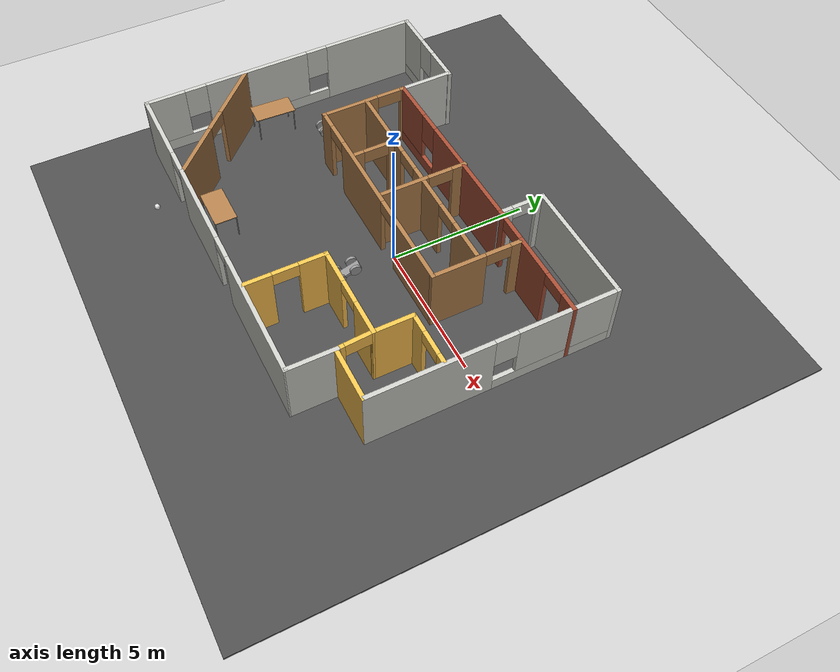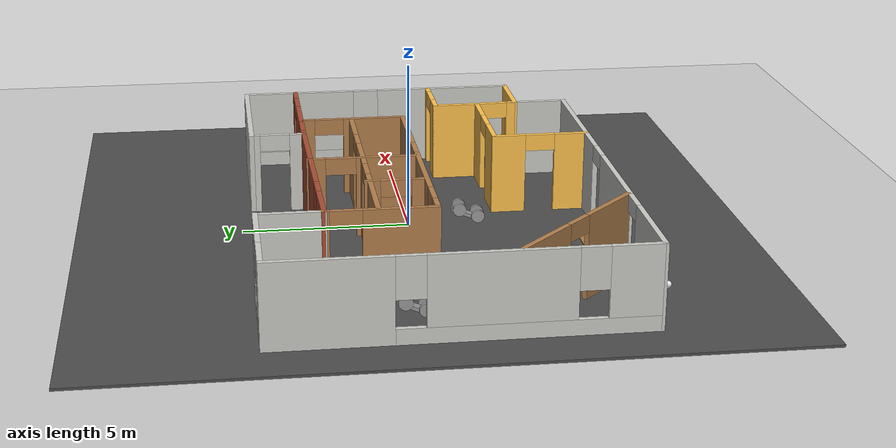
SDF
<sdf version="1.6">
 <world name="default">
  <plugin name="welcome" filename="libwelcome.so"/>
  <light name="sun" type="directional">
   <pose>0 0 10 0 -0 0</pose>
   <diffuse>0.8 0.8 0.8 1</diffuse>
   <specular>0.2 0.2 0.2 1</specular>
   <attenuation>
    <range>1000</range>
    <constant>0.9</constant>
    <linear>0.01</linear>
    <quadratic>0.001</quadratic>
   </attenuation>
   <direction>-0.5 0.1 -0.9</direction>
  </light>
  <model name="ground_plane">
   <static>1</static>
   <link name="link">
    <collision name="collision">
     <geometry><plane><normal>0 0 1</normal><size>100 100</size></plane></geometry>
     <surface>
      <contact><collide_bitmask>65535</collide_bitmask></contact>
      <friction><ode><mu>100</mu><mu2>50</mu2></ode></friction>
     </surface>
    </collision>
    <visual name="visual">
     <cast_shadows>0</cast_shadows>
     <geometry><plane><normal>0 0 1</normal><size>100 100</size></plane></geometry>
     <material>
      <script><uri>file://media/materials/scripts/gazebo.material</uri><name>Gazebo/Grey</name></script>
     </material>
    </visual>
   </link>
  </model>
  <gravity>0 0 -9.8</gravity>
  <magnetic_field>6e-06 2.3e-05 -4.2e-05</magnetic_field>
  <atmosphere type="adiabatic"/>
  <physics name="default_physics" default="0" type="ode">
   <max_step_size>0.001</max_step_size>
   <real_time_factor>1</real_time_factor>
   <real_time_update_rate>1000</real_time_update_rate>
  </physics>
  <scene><ambient>0.4 0.4 0.4 1</ambient><background>0.7 0.7 0.7 1</background><shadows>1</shadows></scene>
  <spherical_coordinates>
   <surface_model>EARTH_WGS84</surface_model>
   <latitude_deg>0</latitude_deg>
   <longitude_deg>0</longitude_deg>
   <elevation>0</elevation>
   <heading_deg>0</heading_deg>
  </spherical_coordinates>
  <model name="s_building">
   <pose>-1.21112 -0.402781 0 0 -0 0</pose>
   <link name="Wall_0">
    <pose>-7.22496 0 0 0 0 -1.56983</pose>
    <visual name="Wall_0_Visual_0">
     <pose>-3.5193 0 1.25 0 -0 0</pose>
     <geometry><box><size>3.4614 0.15 2.5</size></box></geometry>
     <material>
      <script><uri>file://media/materials/scripts/gazebo.material</uri><name>Gazebo/CeilingTiled</name></script>
      <ambient>1 0.764706 0.305882 1</ambient>
     </material>
     <meta><layer>0</layer></meta>
    </visual>
    <collision name="Wall_0_Collision_0">
     <geometry><box><size>3.4614 0.15 2.5</size></box></geometry>
     <pose>-3.5193 0 1.25 0 -0 0</pose>
    </collision>
    <visual name="Wall_0_Visual_1">
     <pose>1.7307 0 0.25 0 -0 0</pose>
     <geometry><box><size>7.0386 0.15 0.5</size></box></geometry>
     <material>
      <script><uri>file://media/materials/scripts/gazebo.material</uri><name>Gazebo/CeilingTiled</name></script>
      <ambient>1 0.764706 0.305882 1</ambient>
     </material>
     <meta><layer>0</layer></meta>
    </visual>
    <collision name="Wall_0_Collision_1">
     <geometry><box><size>7.0386 0.15 0.5</size></box></geometry>
     <pose>1.7307 0 0.25 0 -0 0</pose>
    </collision>
    <visual name="Wall_0_Visual_2">
     <pose>0.984095 0 1.5 0 -0 0</pose>
     <geometry><box><size>3.94539 0.15 2</size></box></geometry>
     <material>
      <script><uri>file://media/materials/scripts/gazebo.material</uri><name>Gazebo/CeilingTiled</name></script>
      <ambient>1 0.764706 0.305882 1</ambient>
     </material>
     <meta><layer>0</layer></meta>
    </visual>
    <collision name="Wall_0_Collision_2">
     <geometry><box><size>3.94539 0.15 2</size></box></geometry>
     <pose>0.984095 0 1.5 0 -0 0</pose>
    </collision>
    <visual name="Wall_0_Visual_3">
     <pose>4.5034 0 1.5 0 -0 0</pose>
     <geometry><box><size>1.49321 0.15 2</size></box></geometry>
     <material>
      <script><uri>file://media/materials/scripts/gazebo.material</uri><name>Gazebo/CeilingTiled</name></script>
      <ambient>1 0.764706 0.305882 1</ambient>
     </material>
     <meta><layer>0</layer></meta>
    </visual>
    <collision name="Wall_0_Collision_3">
     <geometry><box><size>1.49321 0.15 2</size></box></geometry>
     <pose>4.5034 0 1.5 0 -0 0</pose>
    </collision>
    <visual name="Wall_0_Visual_4">
     <pose>-1.3886 0 1.9 0 -0 0</pose>
     <geometry><box><size>0.8 0.15 1.2</size></box></geometry>
     <material>
      <script><uri>file://media/materials/scripts/gazebo.material</uri><name>Gazebo/CeilingTiled</name></script>
      <ambient>1 0.764706 0.305882 1</ambient>
     </material>
     <meta><layer>0</layer></meta>
    </visual>
    <collision name="Wall_0_Collision_4">
     <geometry><box><size>0.8 0.15 1.2</size></box></geometry>
     <pose>-1.3886 0 1.9 0 -0 0</pose>
    </collision>
    <visual name="Wall_0_Visual_5">
     <pose>3.35679 0 1.9 0 -0 0</pose>
     <geometry><box><size>0.8 0.15 1.2</size></box></geometry>
     <material>
      <script><uri>file://media/materials/scripts/gazebo.material</uri><name>Gazebo/CeilingTiled</name></script>
      <ambient>1 0.764706 0.305882 1</ambient>
     </material>
     <meta><layer>0</layer></meta>
    </visual>
    <collision name="Wall_0_Collision_5">
     <geometry><box><size>0.8 0.15 1.2</size></box></geometry>
     <pose>3.35679 0 1.9 0 -0 0</pose>
    </collision>
   </link>
   <link name="Wall_1">
    <pose>-0.928655 -5.175 0 0 -0 0</pose>
    <visual name="Wall_1_Visual_0">
     <pose>-4.95324 0 1.25 0 -0 0</pose>
     <geometry><box><size>2.82615 0.15 2.5</size></box></geometry>
     <material>
      <script><uri>file://media/materials/scripts/gazebo.material</uri><name>Gazebo/CeilingTiled</name></script>
      <ambient>1 0.764706 0.305882 1</ambient>
     </material>
     <meta><layer>0</layer></meta>
    </visual>
    <collision name="Wall_1_Collision_0">
     <geometry><box><size>2.82615 0.15 2.5</size></box></geometry>
     <pose>-4.95324 0 1.25 0 -0 0</pose>
    </collision>
    <visual name="Wall_1_Visual_1">
     <pose>-0.973326 0 1.25 0 -0 0</pose>
     <geometry><box><size>3.33368 0.15 2.5</size></box></geometry>
     <material>
      <script><uri>file://media/materials/scripts/gazebo.material</uri><name>Gazebo/CeilingTiled</name></script>
      <ambient>1 0.764706 0.305882 1</ambient>
     </material>
     <meta><layer>0</layer></meta>
    </visual>
    <collision name="Wall_1_Collision_1">
     <geometry><box><size>3.33368 0.15 2.5</size></box></geometry>
     <pose>-0.973326 0 1.25 0 -0 0</pose>
    </collision>
    <visual name="Wall_1_Visual_2">
     <pose>3.97991 0 1.25 0 -0 0</pose>
     <geometry><box><size>4.7728 0.15 2.5</size></box></geometry>
     <material>
      <script><uri>file://media/materials/scripts/gazebo.material</uri><name>Gazebo/CeilingTiled</name></script>
      <ambient>1 0.764706 0.305882 1</ambient>
     </material>
     <meta><layer>0</layer></meta>
    </visual>
    <collision name="Wall_1_Collision_2">
     <geometry><box><size>4.7728 0.15 2.5</size></box></geometry>
     <pose>3.97991 0 1.25 0 -0 0</pose>
    </collision>
    <visual name="Wall_1_Visual_3">
     <pose>-3.09016 0 2.25 0 -0 0</pose>
     <geometry><box><size>0.9 0.15 0.5</size></box></geometry>
     <material>
      <script><uri>file://media/materials/scripts/gazebo.material</uri><name>Gazebo/CeilingTiled</name></script>
      <ambient>1 0.764706 0.305882 1</ambient>
     </material>
     <meta><layer>0</layer></meta>
    </visual>
    <collision name="Wall_1_Collision_3">
     <geometry><box><size>0.9 0.15 0.5</size></box></geometry>
     <pose>-3.09016 0 2.25 0 -0 0</pose>
    </collision>
    <visual name="Wall_1_Visual_4">
     <pose>1.14351 0 2.25 0 -0 0</pose>
     <geometry><box><size>0.9 0.15 0.5</size></box></geometry>
     <material>
      <script><uri>file://media/materials/scripts/gazebo.material</uri><name>Gazebo/CeilingTiled</name></script>
      <ambient>1 0.764706 0.305882 1</ambient>
     </material>
     <meta><layer>0</layer></meta>
    </visual>
    <collision name="Wall_1_Collision_4">
     <geometry><box><size>0.9 0.15 0.5</size></box></geometry>
     <pose>1.14351 0 2.25 0 -0 0</pose>
    </collision>
   </link>
   <link name="Wall_11">
    <pose>5.05504 3.425 0 0 -0 0</pose>
    <visual name="Wall_11_Visual_0">
     <pose>-2.0487 0 1.25 0 -0 0</pose>
     <geometry><box><size>0.402592 0.15 2.5</size></box></geometry>
     <material>
      <script><uri>file://media/materials/scripts/gazebo.material</uri><name>Gazebo/Bricks</name></script>
      <ambient>1 0.764706 0.305882 1</ambient>
     </material>
     <meta><layer>0</layer></meta>
    </visual>
    <collision name="Wall_11_Collision_0">
     <geometry><box><size>0.402592 0.15 2.5</size></box></geometry>
     <pose>-2.0487 0 1.25 0 -0 0</pose>
    </collision>
    <visual name="Wall_11_Visual_1">
     <pose>-0.141263 0 1.25 0 -0 0</pose>
     <geometry><box><size>1.61229 0.15 2.5</size></box></geometry>
     <material>
      <script><uri>file://media/materials/scripts/gazebo.material</uri><name>Gazebo/Bricks</name></script>
      <ambient>1 0.764706 0.305882 1</ambient>
     </material>
     <meta><layer>0</layer></meta>
    </visual>
    <collision name="Wall_11_Collision_1">
     <geometry><box><size>1.61229 0.15 2.5</size></box></geometry>
     <pose>-0.141263 0 1.25 0 -0 0</pose>
    </collision>
    <visual name="Wall_11_Visual_2">
     <pose>1.90744 0 1.25 0 -0 0</pose>
     <geometry><box><size>0.685117 0.15 2.5</size></box></geometry>
     <material>
      <script><uri>file://media/materials/scripts/gazebo.material</uri><name>Gazebo/Bricks</name></script>
      <ambient>1 0.764706 0.305882 1</ambient>
     </material>
     <meta><layer>0</layer></meta>
    </visual>
    <collision name="Wall_11_Collision_2">
     <geometry><box><size>0.685117 0.15 2.5</size></box></geometry>
     <pose>1.90744 0 1.25 0 -0 0</pose>
    </collision>
    <visual name="Wall_11_Visual_3">
     <pose>-1.39741 0 2.25 0 -0 0</pose>
     <geometry><box><size>0.9 0.15 0.5</size></box></geometry>
     <material>
      <script><uri>file://media/materials/scripts/gazebo.material</uri><name>Gazebo/Bricks</name></script>
      <ambient>1 0.764706 0.305882 1</ambient>
     </material>
     <meta><layer>0</layer></meta>
    </visual>
    <collision name="Wall_11_Collision_3">
     <geometry><box><size>0.9 0.15 0.5</size></box></geometry>
     <pose>-1.39741 0 2.25 0 -0 0</pose>
    </collision>
    <visual name="Wall_11_Visual_4">
     <pose>1.11488 0 2.25 0 -0 0</pose>
     <geometry><box><size>0.9 0.15 0.5</size></box></geometry>
     <material>
      <script><uri>file://media/materials/scripts/gazebo.material</uri><name>Gazebo/Bricks</name></script>
      <ambient>1 0.764706 0.305882 1</ambient>
     </material>
     <meta><layer>0</layer></meta>
    </visual>
    <collision name="Wall_11_Collision_4">
     <geometry><box><size>0.9 0.15 0.5</size></box></geometry>
     <pose>1.11488 0 2.25 0 -0 0</pose>
    </collision>
   </link>
   <link name="Wall_13">
    <pose>-3.86997 1.775 0 0 0 -1.5708</pose>
    <visual name="Wall_13_Visual_0">
     <pose>-1.5189 0 1.25 0 -0 0</pose>
     <geometry><box><size>0.212208 0.15 2.5</size></box></geometry>
     <material>
      <script><uri>file://media/materials/scripts/gazebo.material</uri><name>Gazebo/Wood</name></script>
      <ambient>1 1 1 1</ambient>
     </material>
     <meta><layer>0</layer></meta>
    </visual>
    <collision name="Wall_13_Collision_0">
     <geometry><box><size>0.212208 0.15 2.5</size></box></geometry>
     <pose>-1.5189 0 1.25 0 -0 0</pose>
    </collision>
    <visual name="Wall_13_Visual_1">
     <pose>0.556104 0 1.25 0 -0 0</pose>
     <geometry><box><size>2.13779 0.15 2.5</size></box></geometry>
     <material>
      <script><uri>file://media/materials/scripts/gazebo.material</uri><name>Gazebo/Wood</name></script>
      <ambient>1 1 1 1</ambient>
     </material>
     <meta><layer>0</layer></meta>
    </visual>
    <collision name="Wall_13_Collision_1">
     <geometry><box><size>2.13779 0.15 2.5</size></box></geometry>
     <pose>0.556104 0 1.25 0 -0 0</pose>
    </collision>
    <visual name="Wall_13_Visual_2">
     <pose>-0.962792 0 2.25 0 -0 0</pose>
     <geometry><box><size>0.9 0.15 0.5</size></box></geometry>
     <material>
      <script><uri>file://media/materials/scripts/gazebo.material</uri><name>Gazebo/Wood</name></script>
      <ambient>1 1 1 1</ambient>
     </material>
     <meta><layer>0</layer></meta>
    </visual>
    <collision name="Wall_13_Collision_2">
     <geometry><box><size>0.9 0.15 0.5</size></box></geometry>
     <pose>-0.962792 0 2.25 0 -0 0</pose>
    </collision>
   </link>
   <link name="Wall_14">
    <pose>0.180036 0.225 0 0 -0 0</pose>
    <visual name="Wall_14_Visual_0">
     <pose>-3.75885 0 1.25 0 -0 0</pose>
     <geometry><box><size>0.732292 0.15 2.5</size></box></geometry>
     <material>
      <script><uri>file://media/materials/scripts/gazebo.material</uri><name>Gazebo/Wood</name></script>
      <ambient>1 1 1 1</ambient>
     </material>
     <meta><layer>0</layer></meta>
    </visual>
    <collision name="Wall_14_Collision_0">
     <geometry><box><size>0.732292 0.15 2.5</size></box></geometry>
     <pose>-3.75885 0 1.25 0 -0 0</pose>
    </collision>
    <visual name="Wall_14_Visual_1">
     <pose>-0.965442 0 1.25 0 -0 0</pose>
     <geometry><box><size>3.05453 0.15 2.5</size></box></geometry>
     <material>
      <script><uri>file://media/materials/scripts/gazebo.material</uri><name>Gazebo/Wood</name></script>
      <ambient>1 1 1 1</ambient>
     </material>
     <meta><layer>0</layer></meta>
    </visual>
    <collision name="Wall_14_Collision_1">
     <geometry><box><size>3.05453 0.15 2.5</size></box></geometry>
     <pose>-0.965442 0 1.25 0 -0 0</pose>
    </collision>
    <visual name="Wall_14_Visual_2">
     <pose>2.79341 0 1.25 0 -0 0</pose>
     <geometry><box><size>2.66318 0.15 2.5</size></box></geometry>
     <material>
      <script><uri>file://media/materials/scripts/gazebo.material</uri><name>Gazebo/Wood</name></script>
      <ambient>1 1 1 1</ambient>
     </material>
     <meta><layer>0</layer></meta>
    </visual>
    <collision name="Wall_14_Collision_2">
     <geometry><box><size>2.66318 0.15 2.5</size></box></geometry>
     <pose>2.79341 0 1.25 0 -0 0</pose>
    </collision>
    <visual name="Wall_14_Visual_3">
     <pose>-2.94271 0 2.25 0 -0 0</pose>
     <geometry><box><size>0.9 0.15 0.5</size></box></geometry>
     <material>
      <script><uri>file://media/materials/scripts/gazebo.material</uri><name>Gazebo/Wood</name></script>
      <ambient>1 1 1 1</ambient>
     </material>
     <meta><layer>0</layer></meta>
    </visual>
    <collision name="Wall_14_Collision_3">
     <geometry><box><size>0.9 0.15 0.5</size></box></geometry>
     <pose>-2.94271 0 2.25 0 -0 0</pose>
    </collision>
    <visual name="Wall_14_Visual_4">
     <pose>1.01182 0 2.25 0 -0 0</pose>
     <geometry><box><size>0.9 0.15 0.5</size></box></geometry>
     <material>
      <script><uri>file://media/materials/scripts/gazebo.material</uri><name>Gazebo/Wood</name></script>
      <ambient>1 1 1 1</ambient>
     </material>
     <meta><layer>0</layer></meta>
    </visual>
    <collision name="Wall_14_Collision_4">
     <geometry><box><size>0.9 0.15 0.5</size></box></geometry>
     <pose>1.01182 0 2.25 0 -0 0</pose>
    </collision>
   </link>
   <link name="Wall_15">
    <pose>4.23004 1.775 0 0 -0 1.5708</pose>
    <visual name="Wall_15_Visual_0">
     <pose>-0.649152 0 1.25 0 -0 0</pose>
     <geometry><box><size>1.9517 0.15 2.5</size></box></geometry>
     <material>
      <script><uri>file://media/materials/scripts/gazebo.material</uri><name>Gazebo/Wood</name></script>
      <ambient>1 1 1 1</ambient>
     </material>
     <meta><layer>0</layer></meta>
    </visual>
    <collision name="Wall_15_Collision_0">
     <geometry><box><size>1.9517 0.15 2.5</size></box></geometry>
     <pose>-0.649152 0 1.25 0 -0 0</pose>
    </collision>
    <visual name="Wall_15_Visual_1">
     <pose>1.42585 0 1.25 0 -0 0</pose>
     <geometry><box><size>0.398304 0.15 2.5</size></box></geometry>
     <material>
      <script><uri>file://media/materials/scripts/gazebo.material</uri><name>Gazebo/Wood</name></script>
      <ambient>1 1 1 1</ambient>
     </material>
     <meta><layer>0</layer></meta>
    </visual>
    <collision name="Wall_15_Collision_1">
     <geometry><box><size>0.398304 0.15 2.5</size></box></geometry>
     <pose>1.42585 0 1.25 0 -0 0</pose>
    </collision>
    <visual name="Wall_15_Visual_2">
     <pose>0.776696 0 2.25 0 -0 0</pose>
     <geometry><box><size>0.9 0.15 0.5</size></box></geometry>
     <material>
      <script><uri>file://media/materials/scripts/gazebo.material</uri><name>Gazebo/Wood</name></script>
      <ambient>1 1 1 1</ambient>
     </material>
     <meta><layer>0</layer></meta>
    </visual>
    <collision name="Wall_15_Collision_2">
     <geometry><box><size>0.9 0.15 0.5</size></box></geometry>
     <pose>0.776696 0 2.25 0 -0 0</pose>
    </collision>
   </link>
   <link name="Wall_17">
    <pose>0.138801 1.85384 0 0 -0 0</pose>
    <visual name="Wall_17_Visual_0">
     <pose>-2.58243 0 1.25 0 -0 0</pose>
     <geometry><box><size>2.83515 0.15 2.5</size></box></geometry>
     <material>
      <script><uri>file://media/materials/scripts/gazebo.material</uri><name>Gazebo/Wood</name></script>
      <ambient>1 1 1 1</ambient>
     </material>
     <meta><layer>0</layer></meta>
    </visual>
    <collision name="Wall_17_Collision_0">
     <geometry><box><size>2.83515 0.15 2.5</size></box></geometry>
     <pose>-2.58243 0 1.25 0 -0 0</pose>
    </collision>
    <visual name="Wall_17_Visual_1">
     <pose>0.657606 0 1.25 0 -0 0</pose>
     <geometry><box><size>1.84491 0.15 2.5</size></box></geometry>
     <material>
      <script><uri>file://media/materials/scripts/gazebo.material</uri><name>Gazebo/Wood</name></script>
      <ambient>1 1 1 1</ambient>
     </material>
     <meta><layer>0</layer></meta>
    </visual>
    <collision name="Wall_17_Collision_1">
     <geometry><box><size>1.84491 0.15 2.5</size></box></geometry>
     <pose>0.657606 0 1.25 0 -0 0</pose>
    </collision>
    <visual name="Wall_17_Visual_2">
     <pose>3.24003 0 1.25 0 -0 0</pose>
     <geometry><box><size>1.51994 0.15 2.5</size></box></geometry>
     <material>
      <script><uri>file://media/materials/scripts/gazebo.material</uri><name>Gazebo/Wood</name></script>
      <ambient>1 1 1 1</ambient>
     </material>
     <meta><layer>0</layer></meta>
    </visual>
    <collision name="Wall_17_Collision_2">
     <geometry><box><size>1.51994 0.15 2.5</size></box></geometry>
     <pose>3.24003 0 1.25 0 -0 0</pose>
    </collision>
    <visual name="Wall_17_Visual_3">
     <pose>-0.71485 0 2.25 0 -0 0</pose>
     <geometry><box><size>0.9 0.15 0.5</size></box></geometry>
     <material>
      <script><uri>file://media/materials/scripts/gazebo.material</uri><name>Gazebo/Wood</name></script>
      <ambient>1 1 1 1</ambient>
     </material>
     <meta><layer>0</layer></meta>
    </visual>
    <collision name="Wall_17_Collision_3">
     <geometry><box><size>0.9 0.15 0.5</size></box></geometry>
     <pose>-0.71485 0 2.25 0 -0 0</pose>
    </collision>
    <visual name="Wall_17_Visual_4">
     <pose>2.03006 0 2.25 0 -0 0</pose>
     <geometry><box><size>0.9 0.15 0.5</size></box></geometry>
     <material>
      <script><uri>file://media/materials/scripts/gazebo.material</uri><name>Gazebo/Wood</name></script>
      <ambient>1 1 1 1</ambient>
     </material>
     <meta><layer>0</layer></meta>
    </visual>
    <collision name="Wall_17_Collision_4">
     <geometry><box><size>0.9 0.15 0.5</size></box></geometry>
     <pose>2.03006 0 2.25 0 -0 0</pose>
    </collision>
   </link>
   <link name="Wall_19">
    <pose>0.447477 1.88565 0 0 0 -1.5708</pose>
    <visual name="Wall_19_Visual_0">
     <pose>-1.34726 0 1.25 0 -0 0</pose>
     <geometry><box><size>0.555478 0.15 2.5</size></box></geometry>
     <material>
      <script><uri>file://media/materials/scripts/gazebo.material</uri><name>Gazebo/Wood</name></script>
      <ambient>1 1 1 1</ambient>
     </material>
     <meta><layer>0</layer></meta>
    </visual>
    <collision name="Wall_19_Collision_0">
     <geometry><box><size>0.555478 0.15 2.5</size></box></geometry>
     <pose>-1.34726 0 1.25 0 -0 0</pose>
    </collision>
    <visual name="Wall_19_Visual_1">
     <pose>0.727739 0 1.25 0 -0 0</pose>
     <geometry><box><size>1.79452 0.15 2.5</size></box></geometry>
     <material>
      <script><uri>file://media/materials/scripts/gazebo.material</uri><name>Gazebo/Wood</name></script>
      <ambient>1 1 1 1</ambient>
     </material>
     <meta><layer>0</layer></meta>
    </visual>
    <collision name="Wall_19_Collision_1">
     <geometry><box><size>1.79452 0.15 2.5</size></box></geometry>
     <pose>0.727739 0 1.25 0 -0 0</pose>
    </collision>
    <visual name="Wall_19_Visual_2">
     <pose>-0.619522 0 2.25 0 -0 0</pose>
     <geometry><box><size>0.9 0.15 0.5</size></box></geometry>
     <material>
      <script><uri>file://media/materials/scripts/gazebo.material</uri><name>Gazebo/Wood</name></script>
      <ambient>1 1 1 1</ambient>
     </material>
     <meta><layer>0</layer></meta>
    </visual>
    <collision name="Wall_19_Collision_2">
     <geometry><box><size>0.9 0.15 0.5</size></box></geometry>
     <pose>-0.619522 0 2.25 0 -0 0</pose>
    </collision>
   </link>
   <link name="Wall_2">
    <collision name="Wall_2_Collision">
     <geometry><box><size>1.75 0.15 2.5</size></box></geometry>
     <pose>0 0 1.25 0 -0 0</pose>
    </collision>
    <visual name="Wall_2_Visual">
     <pose>0 0 1.25 0 -0 0</pose>
     <geometry><box><size>1.75 0.15 2.5</size></box></geometry>
     <material>
      <script><uri>file://media/materials/scripts/gazebo.material</uri><name>Gazebo/CeilingTiled</name></script>
      <ambient>1 0.764706 0.305882 1</ambient>
     </material>
     <meta><layer>0</layer></meta>
    </visual>
    <pose>5.36266 -4.32848 0 0 -0 1.5708</pose>
   </link>
   <link name="Wall_21">
    <pose>-1.59957 1.14688 0 0 0 -1.5708</pose>
    <visual name="Wall_21_Visual_0">
     <pose>-0.643785 0 1.25 0 -0 0</pose>
     <geometry><box><size>0.46243 0.15 2.5</size></box></geometry>
     <material>
      <script><uri>file://media/materials/scripts/gazebo.material</uri><name>Gazebo/Wood</name></script>
      <ambient>1 1 1 1</ambient>
     </material>
     <meta><layer>0</layer></meta>
    </visual>
    <collision name="Wall_21_Collision_0">
     <geometry><box><size>0.46243 0.15 2.5</size></box></geometry>
     <pose>-0.643785 0 1.25 0 -0 0</pose>
    </collision>
    <visual name="Wall_21_Visual_1">
     <pose>0.681215 0 1.25 0 -0 0</pose>
     <geometry><box><size>0.38757 0.15 2.5</size></box></geometry>
     <material>
      <script><uri>file://media/materials/scripts/gazebo.material</uri><name>Gazebo/Wood</name></script>
      <ambient>1 1 1 1</ambient>
     </material>
     <meta><layer>0</layer></meta>
    </visual>
    <collision name="Wall_21_Collision_1">
     <geometry><box><size>0.38757 0.15 2.5</size></box></geometry>
     <pose>0.681215 0 1.25 0 -0 0</pose>
    </collision>
    <visual name="Wall_21_Visual_2">
     <pose>0.03743 0 2.25 0 -0 0</pose>
     <geometry><box><size>0.9 0.15 0.5</size></box></geometry>
     <material>
      <script><uri>file://media/materials/scripts/gazebo.material</uri><name>Gazebo/Wood</name></script>
      <ambient>1 1 1 1</ambient>
     </material>
     <meta><layer>0</layer></meta>
    </visual>
    <collision name="Wall_21_Collision_2">
     <geometry><box><size>0.9 0.15 0.5</size></box></geometry>
     <pose>0.03743 0 2.25 0 -0 0</pose>
    </collision>
   </link>
   <link name="Wall_23">
    <pose>-5.3328 -3.29901 0 0 0 -0.785398</pose>
    <visual name="Wall_23_Visual_0">
     <pose>-1.5295 0 1.25 0 -0 0</pose>
     <geometry><box><size>2.191 0.15 2.5</size></box></geometry>
     <material>
      <script><uri>file://media/materials/scripts/gazebo.material</uri><name>Gazebo/Wood</name></script>
      <ambient>1 1 1 1</ambient>
     </material>
     <meta><layer>0</layer></meta>
    </visual>
    <collision name="Wall_23_Collision_0">
     <geometry><box><size>2.191 0.15 2.5</size></box></geometry>
     <pose>-1.5295 0 1.25 0 -0 0</pose>
    </collision>
    <visual name="Wall_23_Visual_1">
     <pose>1.5455 0 1.25 0 -0 0</pose>
     <geometry><box><size>2.15901 0.15 2.5</size></box></geometry>
     <material>
      <script><uri>file://media/materials/scripts/gazebo.material</uri><name>Gazebo/Wood</name></script>
      <ambient>1 1 1 1</ambient>
     </material>
     <meta><layer>0</layer></meta>
    </visual>
    <collision name="Wall_23_Collision_1">
     <geometry><box><size>2.15901 0.15 2.5</size></box></geometry>
     <pose>1.5455 0 1.25 0 -0 0</pose>
    </collision>
    <visual name="Wall_23_Visual_2">
     <pose>0.015995 0 2.25 0 -0 0</pose>
     <geometry><box><size>0.9 0.15 0.5</size></box></geometry>
     <material>
      <script><uri>file://media/materials/scripts/gazebo.material</uri><name>Gazebo/Wood</name></script>
      <ambient>1 1 1 1</ambient>
     </material>
     <meta><layer>0</layer></meta>
    </visual>
    <collision name="Wall_23_Collision_2">
     <geometry><box><size>0.9 0.15 0.5</size></box></geometry>
     <pose>0.015995 0 2.25 0 -0 0</pose>
    </collision>
   </link>
   <link name="Wall_25">
    <pose>1.93624 -3.74627 0 0 -0 1.5708</pose>
    <visual name="Wall_25_Visual_0">
     <pose>-0.966379 0 1.25 0 -0 0</pose>
     <geometry><box><size>1.06724 0.15 2.5</size></box></geometry>
     <material>
      <script><uri>file://media/materials/scripts/gazebo.material</uri><name>Gazebo/Grey</name></script>
      <ambient>1 0.764706 0.305882 1</ambient>
     </material>
     <meta><layer>0</layer></meta>
    </visual>
    <collision name="Wall_25_Collision_0">
     <geometry><box><size>1.06724 0.15 2.5</size></box></geometry>
     <pose>-0.966379 0 1.25 0 -0 0</pose>
    </collision>
    <visual name="Wall_25_Visual_1">
     <pose>0.983621 0 1.25 0 -0 0</pose>
     <geometry><box><size>1.03276 0.15 2.5</size></box></geometry>
     <material>
      <script><uri>file://media/materials/scripts/gazebo.material</uri><name>Gazebo/Grey</name></script>
      <ambient>1 0.764706 0.305882 1</ambient>
     </material>
     <meta><layer>0</layer></meta>
    </visual>
    <collision name="Wall_25_Collision_1">
     <geometry><box><size>1.03276 0.15 2.5</size></box></geometry>
     <pose>0.983621 0 1.25 0 -0 0</pose>
    </collision>
    <visual name="Wall_25_Visual_2">
     <pose>0.017241 0 2.25 0 -0 0</pose>
     <geometry><box><size>0.9 0.15 0.5</size></box></geometry>
     <material>
      <script><uri>file://media/materials/scripts/gazebo.material</uri><name>Gazebo/Grey</name></script>
      <ambient>1 0.764706 0.305882 1</ambient>
     </material>
     <meta><layer>0</layer></meta>
    </visual>
    <collision name="Wall_25_Collision_2">
     <geometry><box><size>0.9 0.15 0.5</size></box></geometry>
     <pose>0.017241 0 2.25 0 -0 0</pose>
    </collision>
   </link>
   <link name="Wall_26">
    <pose>3.61124 -2.32127 0 0 -0 0</pose>
    <visual name="Wall_26_Visual_0">
     <pose>-1.10007 0 1.25 0 -0 0</pose>
     <geometry><box><size>1.29986 0.15 2.5</size></box></geometry>
     <material>
      <script><uri>file://media/materials/scripts/gazebo.material</uri><name>Gazebo/Grey</name></script>
      <ambient>1 0.764706 0.305882 1</ambient>
     </material>
     <meta><layer>0</layer></meta>
    </visual>
    <collision name="Wall_26_Collision_0">
     <geometry><box><size>1.29986 0.15 2.5</size></box></geometry>
     <pose>-1.10007 0 1.25 0 -0 0</pose>
    </collision>
    <visual name="Wall_26_Visual_1">
     <pose>1.09993 0 1.25 0 -0 0</pose>
     <geometry><box><size>1.30014 0.15 2.5</size></box></geometry>
     <material>
      <script><uri>file://media/materials/scripts/gazebo.material</uri><name>Gazebo/Grey</name></script>
      <ambient>1 0.764706 0.305882 1</ambient>
     </material>
     <meta><layer>0</layer></meta>
    </visual>
    <collision name="Wall_26_Collision_1">
     <geometry><box><size>1.30014 0.15 2.5</size></box></geometry>
     <pose>1.09993 0 1.25 0 -0 0</pose>
    </collision>
    <visual name="Wall_26_Visual_2">
     <pose>-0.000139 0 2.25 0 -0 0</pose>
     <geometry><box><size>0.9 0.15 0.5</size></box></geometry>
     <material>
      <script><uri>file://media/materials/scripts/gazebo.material</uri><name>Gazebo/Grey</name></script>
      <ambient>1 0.764706 0.305882 1</ambient>
     </material>
     <meta><layer>0</layer></meta>
    </visual>
    <collision name="Wall_26_Collision_2">
     <geometry><box><size>0.9 0.15 0.5</size></box></geometry>
     <pose>-0.000139 0 2.25 0 -0 0</pose>
    </collision>
   </link>
   <link name="Wall_27">
    <collision name="Wall_27_Collision">
     <geometry><box><size>1.5 0.15 2.5</size></box></geometry>
     <pose>0 0 1.25 0 -0 0</pose>
    </collision>
    <visual name="Wall_27_Visual">
     <pose>0 0 1.25 0 -0 0</pose>
     <geometry><box><size>1.5 0.15 2.5</size></box></geometry>
     <material>
      <script><uri>file://media/materials/scripts/gazebo.material</uri><name>Gazebo/Grey</name></script>
      <ambient>1 0.764706 0.305882 1</ambient>
     </material>
     <meta><layer>0</layer></meta>
    </visual>
    <pose>5.28624 -1.64627 0 0 -0 1.5708</pose>
   </link>
   <link name="Wall_28">
    <pose>6.21124 -0.971274 0 0 -0 0</pose>
    <visual name="Wall_28_Visual_0">
     <pose>-0.629352 0 1.25 0 -0 0</pose>
     <geometry><box><size>0.741296 0.15 2.5</size></box></geometry>
     <material>
      <script><uri>file://media/materials/scripts/gazebo.material</uri><name>Gazebo/Grey</name></script>
      <ambient>1 0.764706 0.305882 1</ambient>
     </material>
     <meta><layer>0</layer></meta>
    </visual>
    <collision name="Wall_28_Collision_0">
     <geometry><box><size>0.741296 0.15 2.5</size></box></geometry>
     <pose>-0.629352 0 1.25 0 -0 0</pose>
    </collision>
    <visual name="Wall_28_Visual_1">
     <pose>0.820648 0 1.25 0 -0 0</pose>
     <geometry><box><size>0.358704 0.15 2.5</size></box></geometry>
     <material>
      <script><uri>file://media/materials/scripts/gazebo.material</uri><name>Gazebo/Grey</name></script>
      <ambient>1 0.764706 0.305882 1</ambient>
     </material>
     <meta><layer>0</layer></meta>
    </visual>
    <collision name="Wall_28_Collision_1">
     <geometry><box><size>0.358704 0.15 2.5</size></box></geometry>
     <pose>0.820648 0 1.25 0 -0 0</pose>
    </collision>
    <visual name="Wall_28_Visual_2">
     <pose>0.191296 0 2.25 0 -0 0</pose>
     <geometry><box><size>0.9 0.15 0.5</size></box></geometry>
     <material>
      <script><uri>file://media/materials/scripts/gazebo.material</uri><name>Gazebo/Grey</name></script>
      <ambient>1 0.764706 0.305882 1</ambient>
     </material>
     <meta><layer>0</layer></meta>
    </visual>
    <collision name="Wall_28_Collision_2">
     <geometry><box><size>0.9 0.15 0.5</size></box></geometry>
     <pose>0.191296 0 2.25 0 -0 0</pose>
    </collision>
   </link>
   <link name="Wall_3">
    <collision name="Wall_3_Collision">
     <geometry><box><size>2.01738 0.15 2.5</size></box></geometry>
     <pose>0 0 1.25 0 -0 0</pose>
    </collision>
    <visual name="Wall_3_Visual">
     <pose>0 0 1.25 0 -0 0</pose>
     <geometry><box><size>2.01738 0.15 2.5</size></box></geometry>
     <material>
      <script><uri>file://media/materials/scripts/gazebo.material</uri><name>Gazebo/Grey</name></script>
      <ambient>1 0.764706 0.305882 1</ambient>
     </material>
     <meta><layer>0</layer></meta>
    </visual>
    <pose>6.29634 -3.575 0 0 -0 0</pose>
   </link>
   <link name="Wall_30">
    <pose>5.32445 -2.94814 0 0 0 -1.50992</pose>
    <visual name="Wall_30_Visual_0">
     <pose>-0.629118 0 1.25 0 -0 0</pose>
     <geometry><box><size>0.147817 0.15 2.5</size></box></geometry>
     <material>
      <script><uri>file://media/materials/scripts/gazebo.material</uri><name>Gazebo/Grey</name></script>
      <ambient>1 0.764706 0.305882 1</ambient>
     </material>
     <meta><layer>0</layer></meta>
    </visual>
    <collision name="Wall_30_Collision_0">
     <geometry><box><size>0.147817 0.15 2.5</size></box></geometry>
     <pose>-0.629118 0 1.25 0 -0 0</pose>
    </collision>
    <visual name="Wall_30_Visual_1">
     <pose>0.523909 0 1.25 0 -0 0</pose>
     <geometry><box><size>0.358236 0.15 2.5</size></box></geometry>
     <material>
      <script><uri>file://media/materials/scripts/gazebo.material</uri><name>Gazebo/Grey</name></script>
      <ambient>1 0.764706 0.305882 1</ambient>
     </material>
     <meta><layer>0</layer></meta>
    </visual>
    <collision name="Wall_30_Collision_1">
     <geometry><box><size>0.358236 0.15 2.5</size></box></geometry>
     <pose>0.523909 0 1.25 0 -0 0</pose>
    </collision>
    <visual name="Wall_30_Visual_2">
     <pose>-0.105209 0 2.25 0 -0 0</pose>
     <geometry><box><size>0.9 0.15 0.5</size></box></geometry>
     <material>
      <script><uri>file://media/materials/scripts/gazebo.material</uri><name>Gazebo/Grey</name></script>
      <ambient>1 0.764706 0.305882 1</ambient>
     </material>
     <meta><layer>0</layer></meta>
    </visual>
    <collision name="Wall_30_Collision_2">
     <geometry><box><size>0.9 0.15 0.5</size></box></geometry>
     <pose>-0.105209 0 2.25 0 -0 0</pose>
    </collision>
   </link>
   <link name="Wall_4">
    <pose>7.23004 0.725 0 0 -0 1.5708</pose>
    <visual name="Wall_4_Visual_0">
     <pose>-2.19527 0 1.25 0 -0 0</pose>
     <geometry><box><size>4.35945 0.15 2.5</size></box></geometry>
     <material>
      <script><uri>file://media/materials/scripts/gazebo.material</uri><name>Gazebo/CeilingTiled</name></script>
      <ambient>1 0.764706 0.305882 1</ambient>
     </material>
     <meta><layer>0</layer></meta>
    </visual>
    <collision name="Wall_4_Collision_0">
     <geometry><box><size>4.35945 0.15 2.5</size></box></geometry>
     <pose>-2.19527 0 1.25 0 -0 0</pose>
    </collision>
    <visual name="Wall_4_Visual_1">
     <pose>2.17973 0 0.25 0 -0 0</pose>
     <geometry><box><size>4.39055 0.15 0.5</size></box></geometry>
     <material>
      <script><uri>file://media/materials/scripts/gazebo.material</uri><name>Gazebo/CeilingTiled</name></script>
      <ambient>1 0.764706 0.305882 1</ambient>
     </material>
     <meta><layer>0</layer></meta>
    </visual>
    <collision name="Wall_4_Collision_1">
     <geometry><box><size>4.39055 0.15 0.5</size></box></geometry>
     <pose>2.17973 0 0.25 0 -0 0</pose>
    </collision>
    <visual name="Wall_4_Visual_2">
     <pose>2.57973 0 1.5 0 -0 0</pose>
     <geometry><box><size>3.59055 0.15 2</size></box></geometry>
     <material>
      <script><uri>file://media/materials/scripts/gazebo.material</uri><name>Gazebo/CeilingTiled</name></script>
      <ambient>1 0.764706 0.305882 1</ambient>
     </material>
     <meta><layer>0</layer></meta>
    </visual>
    <collision name="Wall_4_Collision_2">
     <geometry><box><size>3.59055 0.15 2</size></box></geometry>
     <pose>2.57973 0 1.5 0 -0 0</pose>
    </collision>
    <visual name="Wall_4_Visual_3">
     <pose>0.384455 0 1.9 0 -0 0</pose>
     <geometry><box><size>0.8 0.15 1.2</size></box></geometry>
     <material>
      <script><uri>file://media/materials/scripts/gazebo.material</uri><name>Gazebo/CeilingTiled</name></script>
      <ambient>1 0.764706 0.305882 1</ambient>
     </material>
     <meta><layer>0</layer></meta>
    </visual>
    <collision name="Wall_4_Collision_3">
     <geometry><box><size>0.8 0.15 1.2</size></box></geometry>
     <pose>0.384455 0 1.9 0 -0 0</pose>
    </collision>
   </link>
   <link name="Wall_5">
    <collision name="Wall_5_Collision">
     <geometry><box><size>4.5 0.15 2.5</size></box></geometry>
     <pose>0 0 1.25 0 -0 0</pose>
    </collision>
    <visual name="Wall_5_Visual">
     <pose>0 0 1.25 0 -0 0</pose>
     <geometry><box><size>4.5 0.15 2.5</size></box></geometry>
     <material>
      <script><uri>file://media/materials/scripts/gazebo.material</uri><name>Gazebo/CeilingTiled</name></script>
      <ambient>1 0.764706 0.305882 1</ambient>
     </material>
     <meta><layer>0</layer></meta>
    </visual>
    <pose>5.05504 5.025 0 0 -0 3.14159</pose>
   </link>
   <link name="Wall_6">
    <pose>2.88004 4.225 0 0 0 -1.5708</pose>
    <visual name="Wall_6_Visual_0">
     <pose>-0.709802 0 1.25 0 -0 0</pose>
     <geometry><box><size>0.330395 0.15 2.5</size></box></geometry>
     <material>
      <script><uri>file://media/materials/scripts/gazebo.material</uri><name>Gazebo/CeilingTiled</name></script>
      <ambient>1 0.764706 0.305882 1</ambient>
     </material>
     <meta><layer>0</layer></meta>
    </visual>
    <collision name="Wall_6_Collision_0">
     <geometry><box><size>0.330395 0.15 2.5</size></box></geometry>
     <pose>-0.709802 0 1.25 0 -0 0</pose>
    </collision>
    <visual name="Wall_6_Visual_1">
     <pose>0.615198 0 1.25 0 -0 0</pose>
     <geometry><box><size>0.519605 0.15 2.5</size></box></geometry>
     <material>
      <script><uri>file://media/materials/scripts/gazebo.material</uri><name>Gazebo/CeilingTiled</name></script>
      <ambient>1 0.764706 0.305882 1</ambient>
     </material>
     <meta><layer>0</layer></meta>
    </visual>
    <collision name="Wall_6_Collision_1">
     <geometry><box><size>0.519605 0.15 2.5</size></box></geometry>
     <pose>0.615198 0 1.25 0 -0 0</pose>
    </collision>
    <visual name="Wall_6_Visual_2">
     <pose>-0.094605 0 2.25 0 -0 0</pose>
     <geometry><box><size>0.9 0.15 0.5</size></box></geometry>
     <material>
      <script><uri>file://media/materials/scripts/gazebo.material</uri><name>Gazebo/CeilingTiled</name></script>
      <ambient>1 0.764706 0.305882 1</ambient>
     </material>
     <meta><layer>0</layer></meta>
    </visual>
    <collision name="Wall_6_Collision_2">
     <geometry><box><size>0.9 0.15 0.5</size></box></geometry>
     <pose>-0.094605 0 2.25 0 -0 0</pose>
    </collision>
   </link>
   <link name="Wall_7">
    <pose>-0.494964 3.375 0 0 0 -3.12678</pose>
    <visual name="Wall_7_Visual_0">
     <pose>-1.23234 0 1.25 0 -0 0</pose>
     <geometry><box><size>4.43698 0.15 2.5</size></box></geometry>
     <material>
      <script><uri>file://media/materials/scripts/gazebo.material</uri><name>Gazebo/Bricks</name></script>
      <ambient>1 1 1 1</ambient>
     </material>
     <meta><layer>0</layer></meta>
    </visual>
    <collision name="Wall_7_Collision_0">
     <geometry><box><size>4.43698 0.15 2.5</size></box></geometry>
     <pose>-1.23234 0 1.25 0 -0 0</pose>
    </collision>
    <visual name="Wall_7_Visual_1">
     <pose>2.21849 0 0.25 0 -0 0</pose>
     <geometry><box><size>2.46468 0.15 0.5</size></box></geometry>
     <material>
      <script><uri>file://media/materials/scripts/gazebo.material</uri><name>Gazebo/Bricks</name></script>
      <ambient>1 1 1 1</ambient>
     </material>
     <meta><layer>0</layer></meta>
    </visual>
    <collision name="Wall_7_Collision_1">
     <geometry><box><size>2.46468 0.15 0.5</size></box></geometry>
     <pose>2.21849 0 0.25 0 -0 0</pose>
    </collision>
    <visual name="Wall_7_Visual_2">
     <pose>2.61849 0 1.5 0 -0 0</pose>
     <geometry><box><size>1.66468 0.15 2</size></box></geometry>
     <material>
      <script><uri>file://media/materials/scripts/gazebo.material</uri><name>Gazebo/Bricks</name></script>
      <ambient>1 1 1 1</ambient>
     </material>
     <meta><layer>0</layer></meta>
    </visual>
    <collision name="Wall_7_Collision_2">
     <geometry><box><size>1.66468 0.15 2</size></box></geometry>
     <pose>2.61849 0 1.5 0 -0 0</pose>
    </collision>
    <visual name="Wall_7_Visual_3">
     <pose>1.38615 0 1.9 0 -0 0</pose>
     <geometry><box><size>0.8 0.15 1.2</size></box></geometry>
     <material>
      <script><uri>file://media/materials/scripts/gazebo.material</uri><name>Gazebo/Bricks</name></script>
      <ambient>1 1 1 1</ambient>
     </material>
     <meta><layer>0</layer></meta>
    </visual>
    <collision name="Wall_7_Collision_3">
     <geometry><box><size>0.8 0.15 1.2</size></box></geometry>
     <pose>1.38615 0 1.9 0 -0 0</pose>
    </collision>
   </link>
   <link name="Wall_8">
    <collision name="Wall_8_Collision">
     <geometry><box><size>2 0.15 2.5</size></box></geometry>
     <pose>0 0 1.25 0 -0 0</pose>
    </collision>
    <visual name="Wall_8_Visual">
     <pose>0 0 1.25 0 -0 0</pose>
     <geometry><box><size>2 0.15 2.5</size></box></geometry>
     <material>
      <script><uri>file://media/materials/scripts/gazebo.material</uri><name>Gazebo/CeilingTiled</name></script>
      <ambient>1 0.764706 0.305882 1</ambient>
     </material>
     <meta><layer>0</layer></meta>
    </visual>
    <pose>-3.86997 4.25 0 0 -0 1.5708</pose>
   </link>
   <link name="Wall_9">
    <pose>-5.52336 5.175 0 0 -0 3.14159</pose>
    <visual name="Wall_9_Visual_0">
     <pose>-1.08539 0 1.25 0 -0 0</pose>
     <geometry><box><size>1.33922 0.15 2.5</size></box></geometry>
     <material>
      <script><uri>file://media/materials/scripts/gazebo.material</uri><name>Gazebo/CeilingTiled</name></script>
      <ambient>1 0.764706 0.305882 1</ambient>
     </material>
     <meta><layer>0</layer></meta>
    </visual>
    <collision name="Wall_9_Collision_0">
     <geometry><box><size>1.33922 0.15 2.5</size></box></geometry>
     <pose>-1.08539 0 1.25 0 -0 0</pose>
    </collision>
    <visual name="Wall_9_Visual_1">
     <pose>0.66961 0 0.25 0 -0 0</pose>
     <geometry><box><size>2.17078 0.15 0.5</size></box></geometry>
     <material>
      <script><uri>file://media/materials/scripts/gazebo.material</uri><name>Gazebo/CeilingTiled</name></script>
      <ambient>1 0.764706 0.305882 1</ambient>
     </material>
     <meta><layer>0</layer></meta>
    </visual>
    <collision name="Wall_9_Collision_1">
     <geometry><box><size>2.17078 0.15 0.5</size></box></geometry>
     <pose>0.66961 0 0.25 0 -0 0</pose>
    </collision>
    <visual name="Wall_9_Visual_2">
     <pose>1.06961 0 1.5 0 -0 0</pose>
     <geometry><box><size>1.37078 0.15 2</size></box></geometry>
     <material>
      <script><uri>file://media/materials/scripts/gazebo.material</uri><name>Gazebo/CeilingTiled</name></script>
      <ambient>1 0.764706 0.305882 1</ambient>
     </material>
     <meta><layer>0</layer></meta>
    </visual>
    <collision name="Wall_9_Collision_2">
     <geometry><box><size>1.37078 0.15 2</size></box></geometry>
     <pose>1.06961 0 1.5 0 -0 0</pose>
    </collision>
    <visual name="Wall_9_Visual_3">
     <pose>-0.01578 0 1.9 0 -0 0</pose>
     <geometry><box><size>0.8 0.15 1.2</size></box></geometry>
     <material>
      <script><uri>file://media/materials/scripts/gazebo.material</uri><name>Gazebo/CeilingTiled</name></script>
      <ambient>1 0.764706 0.305882 1</ambient>
     </material>
     <meta><layer>0</layer></meta>
    </visual>
    <collision name="Wall_9_Collision_3">
     <geometry><box><size>0.8 0.15 1.2</size></box></geometry>
     <pose>-0.01578 0 1.9 0 -0 0</pose>
    </collision>
   </link>
   <static>1</static>
  </model>
  <model name="table">
   <static>1</static>
   <link name="link">
    <collision name="surface">
     <pose>0 0 1 0 -0 0</pose>
     <geometry><box><size>1.5 0.8 0.03</size></box></geometry>
     <surface><friction><ode><mu>0.6</mu><mu2>0.6</mu2></ode></friction></surface>
    </collision>
    <visual name="visual1">
     <pose>0 0 1 0 -0 0</pose>
     <geometry><box><size>1.5 0.8 0.03</size></box></geometry>
     <material>
      <script><uri>file://media/materials/scripts/gazebo.material</uri><name>Gazebo/Wood</name></script>
     </material>
    </visual>
    <collision name="front_left_leg">
     <pose>0.68 0.38 0.5 0 -0 0</pose>
     <geometry><cylinder><radius>0.02</radius><length>1</length></cylinder></geometry>
    </collision>
    <visual name="front_left_leg">
     <pose>0.68 0.38 0.5 0 -0 0</pose>
     <geometry><cylinder><radius>0.02</radius><length>1</length></cylinder></geometry>
     <material>
      <script><uri>file://media/materials/scripts/gazebo.material</uri><name>Gazebo/Grey</name></script>
     </material>
    </visual>
    <collision name="front_right_leg">
     <pose>0.68 -0.38 0.5 0 -0 0</pose>
     <geometry><cylinder><radius>0.02</radius><length>1</length></cylinder></geometry>
    </collision>
    <visual name="front_right_leg">
     <pose>0.68 -0.38 0.5 0 -0 0</pose>
     <geometry><cylinder><radius>0.02</radius><length>1</length></cylinder></geometry>
     <material>
      <script><uri>file://media/materials/scripts/gazebo.material</uri><name>Gazebo/Grey</name></script>
     </material>
    </visual>
    <collision name="back_right_leg">
     <pose>-0.68 -0.38 0.5 0 -0 0</pose>
     <geometry><cylinder><radius>0.02</radius><length>1</length></cylinder></geometry>
    </collision>
    <visual name="back_right_leg">
     <pose>-0.68 -0.38 0.5 0 -0 0</pose>
     <geometry><cylinder><radius>0.02</radius><length>1</length></cylinder></geometry>
     <material>
      <script><uri>file://media/materials/scripts/gazebo.material</uri><name>Gazebo/Grey</name></script>
     </material>
    </visual>
    <collision name="back_left_leg">
     <pose>-0.68 0.38 0.5 0 -0 0</pose>
     <geometry><cylinder><radius>0.02</radius><length>1</length></cylinder></geometry>
    </collision>
    <visual name="back_left_leg">
     <pose>-0.68 0.38 0.5 0 -0 0</pose>
     <geometry><cylinder><radius>0.02</radius><length>1</length></cylinder></geometry>
     <material>
      <script><uri>file://media/materials/scripts/gazebo.material</uri><name>Gazebo/Grey</name></script>
     </material>
    </visual>
   </link>
   <pose>-4.01455 -4.73402 0 0 -0 0</pose>
  </model>
  <model name="table_0">
   <static>1</static>
   <link name="link">
    <collision name="surface">
     <pose>0 0 1 0 -0 0</pose>
     <geometry><box><size>1.5 0.8 0.03</size></box></geometry>
     <surface><friction><ode><mu>0.6</mu><mu2>0.6</mu2></ode></friction></surface>
    </collision>
    <visual name="visual1">
     <pose>0 0 1 0 -0 0</pose>
     <geometry><box><size>1.5 0.8 0.03</size></box></geometry>
     <material>
      <script><uri>file://media/materials/scripts/gazebo.material</uri><name>Gazebo/Wood</name></script>
     </material>
    </visual>
    <collision name="front_left_leg">
     <pose>0.68 0.38 0.5 0 -0 0</pose>
     <geometry><cylinder><radius>0.02</radius><length>1</length></cylinder></geometry>
    </collision>
    <visual name="front_left_leg">
     <pose>0.68 0.38 0.5 0 -0 0</pose>
     <geometry><cylinder><radius>0.02</radius><length>1</length></cylinder></geometry>
     <material>
      <script><uri>file://media/materials/scripts/gazebo.material</uri><name>Gazebo/Grey</name></script>
     </material>
    </visual>
    <collision name="front_right_leg">
     <pose>0.68 -0.38 0.5 0 -0 0</pose>
     <geometry><cylinder><radius>0.02</radius><length>1</length></cylinder></geometry>
    </collision>
    <visual name="front_right_leg">
     <pose>0.68 -0.38 0.5 0 -0 0</pose>
     <geometry><cylinder><radius>0.02</radius><length>1</length></cylinder></geometry>
     <material>
      <script><uri>file://media/materials/scripts/gazebo.material</uri><name>Gazebo/Grey</name></script>
     </material>
    </visual>
    <collision name="back_right_leg">
     <pose>-0.68 -0.38 0.5 0 -0 0</pose>
     <geometry><cylinder><radius>0.02</radius><length>1</length></cylinder></geometry>
    </collision>
    <visual name="back_right_leg">
     <pose>-0.68 -0.38 0.5 0 -0 0</pose>
     <geometry><cylinder><radius>0.02</radius><length>1</length></cylinder></geometry>
     <material>
      <script><uri>file://media/materials/scripts/gazebo.material</uri><name>Gazebo/Grey</name></script>
     </material>
    </visual>
    <collision name="back_left_leg">
     <pose>-0.68 0.38 0.5 0 -0 0</pose>
     <geometry><cylinder><radius>0.02</radius><length>1</length></cylinder></geometry>
    </collision>
    <visual name="back_left_leg">
     <pose>-0.68 0.38 0.5 0 -0 0</pose>
     <geometry><cylinder><radius>0.02</radius><length>1</length></cylinder></geometry>
     <material>
      <script><uri>file://media/materials/scripts/gazebo.material</uri><name>Gazebo/Grey</name></script>
     </material>
    </visual>
   </link>
   <pose>-7.72892 -1.19279 0 0 0 -1.61831</pose>
  </model>
  <model name="asphalt_plane">
   <static>1</static>
   <link name="link">
    <collision name="collision"><geometry><box><size>20 20 0.1</size></box></geometry></collision>
    <visual name="visual">
     <cast_shadows>0</cast_shadows>
     <geometry><box><size>20 20 0.1</size></box></geometry>
     <material>
      <script>
       <uri>model://asphalt_plane/materials/scripts</uri>
       <uri>model://asphalt_plane/materials/textures</uri>
       <name>vrc/asphalt</name>
      </script>
     </material>
    </visual>
   </link>
   <pose>0.120009 -0.032107 0 0 -0 0</pose>
  </model>
  <model name="myrobot">
   <link name="link_0">
    <pose>1.89771 0.363402 0 0 -0 0</pose>
    <inertial>
     <mass>1</mass>
     <inertia>
      <ixx>0.166667</ixx>
      <ixy>0</ixy>
      <ixz>0</ixz>
      <iyy>0.166667</iyy>
      <iyz>0</iyz>
      <izz>0.166667</izz>
     </inertia>
     <pose>0 0 0.2 0 -0 0</pose>
    </inertial>
    <visual name="visual">
     <geometry><box><size>0.3 1 0.1</size></box></geometry>
     <material>
      <lighting>1</lighting>
      <script><uri>file://media/materials/scripts/gazebo.material</uri><name>Gazebo/Grey</name></script>
      <shader type="pixel"><normal_map>__default__</normal_map></shader>
      <ambient>0.3 0.3 0.3 1</ambient>
      <diffuse>0.7 0.7 0.7 1</diffuse>
      <specular>0.01 0.01 0.01 1</specular>
      <emissive>0 0 0 1</emissive>
     </material>
    </visual>
    <collision name="collision">
     <geometry><box><size>0.3 1 0.1</size></box></geometry>
     <surface>
      <friction>
       <ode><mu>1</mu><mu2>1</mu2><fdir1>0 0 0</fdir1><slip1>0</slip1><slip2>0</slip2></ode>
       <torsional>
        <coefficient>1</coefficient>
        <patch_radius>0</patch_radius>
        <surface_radius>0</surface_radius>
        <use_patch_radius>1</use_patch_radius>
        <ode><slip>0</slip></ode>
       </torsional>
      </friction>
      <bounce><restitution_coefficient>0</restitution_coefficient><threshold>1e+06</threshold></bounce>
      <contact>
       <collide_without_contact>0</collide_without_contact>
       <collide_without_contact_bitmask>1</collide_without_contact_bitmask>
       <collide_bitmask>1</collide_bitmask>
       <ode>
        <soft_cfm>0</soft_cfm>
        <soft_erp>0.2</soft_erp>
        <kp>1e+13</kp>
        <kd>1</kd>
        <max_vel>0.01</max_vel>
        <min_depth>0</min_depth>
       </ode>
       <bullet>
        <split_impulse>1</split_impulse>
        <split_impulse_penetration_threshold>-0.01</split_impulse_penetration_threshold>
        <soft_cfm>0</soft_cfm>
        <soft_erp>0.2</soft_erp>
        <kp>1e+13</kp>
        <kd>1</kd>
       </bullet>
      </contact>
     </surface>
    </collision>
   </link>
   <link name="link_1_clone_clone_0">
    <pose>1.69765 -0.136569 0.1 4.8e-05 1.5707 1.57075</pose>
    <inertial>
     <mass>1</mass>
     <inertia><ixx>0.145833</ixx><ixy>0</ixy><ixz>0</ixz><iyy>0.145833</iyy><iyz>0</iyz><izz>0.125</izz></inertia>
     <pose>0 0 0.2 -0 1.5707 1.5707</pose>
    </inertial>
    <visual name="visual">
     <pose>0 0 0.2 1.5707 -0 0</pose>
     <geometry><cylinder><radius>0.2</radius><length>0.1</length></cylinder></geometry>
     <material>
      <lighting>1</lighting>
      <script><uri>file://media/materials/scripts/gazebo.material</uri><name>Gazebo/Grey</name></script>
      <shader type="pixel"><normal_map>__default__</normal_map></shader>
      <ambient>0.3 0.3 0.3 1</ambient>
      <diffuse>0.7 0.7 0.7 1</diffuse>
      <specular>0.01 0.01 0.01 1</specular>
      <emissive>0 0 0 1</emissive>
     </material>
    </visual>
    <collision name="collision">
     <pose>0 0 0.2 1.5707 -0 0</pose>
     <geometry><cylinder><radius>0.2</radius><length>0.1</length></cylinder></geometry>
     <surface>
      <friction>
       <ode><mu>1</mu><mu2>1</mu2><fdir1>0 0 0</fdir1><slip1>0</slip1><slip2>0</slip2></ode>
       <torsional>
        <coefficient>1</coefficient>
        <patch_radius>0</patch_radius>
        <surface_radius>0</surface_radius>
        <use_patch_radius>1</use_patch_radius>
        <ode><slip>0</slip></ode>
       </torsional>
      </friction>
      <bounce><restitution_coefficient>0</restitution_coefficient><threshold>1e+06</threshold></bounce>
      <contact>
       <collide_without_contact>0</collide_without_contact>
       <collide_without_contact_bitmask>1</collide_without_contact_bitmask>
       <collide_bitmask>1</collide_bitmask>
       <ode>
        <soft_cfm>0</soft_cfm>
        <soft_erp>0.2</soft_erp>
        <kp>1e+13</kp>
        <kd>1</kd>
        <max_vel>0.01</max_vel>
        <min_depth>0</min_depth>
       </ode>
       <bullet>
        <split_impulse>1</split_impulse>
        <split_impulse_penetration_threshold>-0.01</split_impulse_penetration_threshold>
        <soft_cfm>0</soft_cfm>
        <soft_erp>0.2</soft_erp>
        <kp>1e+13</kp>
        <kd>1</kd>
       </bullet>
      </contact>
     </surface>
    </collision>
   </link>
   <link name="link_1_clone_clone_0_clone">
    <pose>2.09773 -0.136569 0.1 -0.000572 1.5707 1.57013</pose>
    <inertial>
     <mass>1</mass>
     <inertia><ixx>0.145833</ixx><ixy>0</ixy><ixz>0</ixz><iyy>0.145833</iyy><iyz>0</iyz><izz>0.125</izz></inertia>
     <pose>0 0 0.2 -0 1.5707 1.5707</pose>
    </inertial>
    <visual name="visual">
     <pose>0 0 0.2 1.5707 -0 0</pose>
     <geometry><cylinder><radius>0.2</radius><length>0.1</length></cylinder></geometry>
     <material>
      <lighting>1</lighting>
      <script><uri>file://media/materials/scripts/gazebo.material</uri><name>Gazebo/Grey</name></script>
      <shader type="pixel"><normal_map>__default__</normal_map></shader>
      <ambient>0.3 0.3 0.3 1</ambient>
      <diffuse>0.7 0.7 0.7 1</diffuse>
      <specular>0.01 0.01 0.01 1</specular>
      <emissive>0 0 0 1</emissive>
     </material>
    </visual>
    <collision name="collision">
     <pose>0 0 0.2 1.5707 -0 0</pose>
     <geometry><cylinder><radius>0.2</radius><length>0.1</length></cylinder></geometry>
     <surface>
      <friction>
       <ode><mu>1</mu><mu2>1</mu2><fdir1>0 0 0</fdir1><slip1>0</slip1><slip2>0</slip2></ode>
       <torsional>
        <coefficient>1</coefficient>
        <patch_radius>0</patch_radius>
        <surface_radius>0</surface_radius>
        <use_patch_radius>1</use_patch_radius>
        <ode><slip>0</slip></ode>
       </torsional>
      </friction>
      <bounce><restitution_coefficient>0</restitution_coefficient><threshold>1e+06</threshold></bounce>
      <contact>
       <collide_without_contact>0</collide_without_contact>
       <collide_without_contact_bitmask>1</collide_without_contact_bitmask>
       <collide_bitmask>1</collide_bitmask>
       <ode>
        <soft_cfm>0</soft_cfm>
        <soft_erp>0.2</soft_erp>
        <kp>1e+13</kp>
        <kd>1</kd>
        <max_vel>0.01</max_vel>
        <min_depth>0</min_depth>
       </ode>
       <bullet>
        <split_impulse>1</split_impulse>
        <split_impulse_penetration_threshold>-0.01</split_impulse_penetration_threshold>
        <soft_cfm>0</soft_cfm>
        <soft_erp>0.2</soft_erp>
        <kp>1e+13</kp>
        <kd>1</kd>
       </bullet>
      </contact>
     </surface>
    </collision>
   </link>
   <link name="link_1_clone_clone_0_clone_0">
    <pose>2.09773 0.463373 0.1 -0.000572 1.5707 1.57013</pose>
    <inertial>
     <mass>1</mass>
     <inertia><ixx>0.145833</ixx><ixy>0</ixy><ixz>0</ixz><iyy>0.145833</iyy><iyz>0</iyz><izz>0.125</izz></inertia>
     <pose>0 0 0.2 -0 1.5707 1.5707</pose>
    </inertial>
    <visual name="visual">
     <pose>0 0 0.2 1.5707 -0 0</pose>
     <geometry><cylinder><radius>0.2</radius><length>0.1</length></cylinder></geometry>
     <material>
      <lighting>1</lighting>
      <script><uri>file://media/materials/scripts/gazebo.material</uri><name>Gazebo/Grey</name></script>
      <shader type="pixel"><normal_map>__default__</normal_map></shader>
      <ambient>0.3 0.3 0.3 1</ambient>
      <diffuse>0.7 0.7 0.7 1</diffuse>
      <specular>0.01 0.01 0.01 1</specular>
      <emissive>0 0 0 1</emissive>
     </material>
    </visual>
    <collision name="collision">
     <pose>0 0 0.2 1.5707 -0 0</pose>
     <geometry><cylinder><radius>0.2</radius><length>0.1</length></cylinder></geometry>
     <surface>
      <friction>
       <ode><mu>1</mu><mu2>1</mu2><fdir1>0 0 0</fdir1><slip1>0</slip1><slip2>0</slip2></ode>
       <torsional>
        <coefficient>1</coefficient>
        <patch_radius>0</patch_radius>
        <surface_radius>0</surface_radius>
        <use_patch_radius>1</use_patch_radius>
        <ode><slip>0</slip></ode>
       </torsional>
      </friction>
      <bounce><restitution_coefficient>0</restitution_coefficient><threshold>1e+06</threshold></bounce>
      <contact>
       <collide_without_contact>0</collide_without_contact>
       <collide_without_contact_bitmask>1</collide_without_contact_bitmask>
       <collide_bitmask>1</collide_bitmask>
       <ode>
        <soft_cfm>0</soft_cfm>
        <soft_erp>0.2</soft_erp>
        <kp>1e+13</kp>
        <kd>1</kd>
        <max_vel>0.01</max_vel>
        <min_depth>0</min_depth>
       </ode>
       <bullet>
        <split_impulse>1</split_impulse>
        <split_impulse_penetration_threshold>-0.01</split_impulse_penetration_threshold>
        <soft_cfm>0</soft_cfm>
        <soft_erp>0.2</soft_erp>
        <kp>1e+13</kp>
        <kd>1</kd>
       </bullet>
      </contact>
     </surface>
    </collision>
   </link>
   <link name="link_1_clone_clone_0_clone_1">
    <pose>1.69765 0.463373 0.1 -0.000572 1.5707 1.57013</pose>
    <inertial>
     <mass>1</mass>
     <inertia><ixx>0.145833</ixx><ixy>0</ixy><ixz>0</ixz><iyy>0.145833</iyy><iyz>0</iyz><izz>0.125</izz></inertia>
     <pose>0 0 0.2 -0 1.5707 1.5707</pose>
    </inertial>
    <visual name="visual">
     <pose>0 0 0.2 1.5707 -0 0</pose>
     <geometry><cylinder><radius>0.2</radius><length>0.1</length></cylinder></geometry>
     <material>
      <lighting>1</lighting>
      <script><uri>file://media/materials/scripts/gazebo.material</uri><name>Gazebo/Grey</name></script>
      <shader type="pixel"><normal_map>__default__</normal_map></shader>
      <ambient>0.3 0.3 0.3 1</ambient>
      <diffuse>0.7 0.7 0.7 1</diffuse>
      <specular>0.01 0.01 0.01 1</specular>
      <emissive>0 0 0 1</emissive>
     </material>
    </visual>
    <collision name="collision">
     <pose>0 0 0.2 1.5707 -0 0</pose>
     <geometry><cylinder><radius>0.2</radius><length>0.1</length></cylinder></geometry>
     <surface>
      <friction>
       <ode><mu>1</mu><mu2>1</mu2><fdir1>0 0 0</fdir1><slip1>0</slip1><slip2>0</slip2></ode>
       <torsional>
        <coefficient>1</coefficient>
        <patch_radius>0</patch_radius>
        <surface_radius>0</surface_radius>
        <use_patch_radius>1</use_patch_radius>
        <ode><slip>0</slip></ode>
       </torsional>
      </friction>
      <bounce><restitution_coefficient>0</restitution_coefficient><threshold>1e+06</threshold></bounce>
      <contact>
       <collide_without_contact>0</collide_without_contact>
       <collide_without_contact_bitmask>1</collide_without_contact_bitmask>
       <collide_bitmask>1</collide_bitmask>
       <ode>
        <soft_cfm>0</soft_cfm>
        <soft_erp>0.2</soft_erp>
        <kp>1e+13</kp>
        <kd>1</kd>
        <max_vel>0.01</max_vel>
        <min_depth>0</min_depth>
       </ode>
       <bullet>
        <split_impulse>1</split_impulse>
        <split_impulse_penetration_threshold>-0.01</split_impulse_penetration_threshold>
        <soft_cfm>0</soft_cfm>
        <soft_erp>0.2</soft_erp>
        <kp>1e+13</kp>
        <kd>1</kd>
       </bullet>
      </contact>
     </surface>
    </collision>
   </link>
   <joint name="link_0_JOINT_5" type="revolute">
    <parent>link_0</parent>
    <child>link_1_clone_clone_0</child>
    <axis>
     <xyz>0 1 0</xyz>
     <use_parent_model_frame>0</use_parent_model_frame>
     <limit>
      <lower>-1.79769e+308</lower>
      <upper>1.79769e+308</upper>
      <effort>-1</effort>
      <velocity>-1</velocity>
     </limit>
     <dynamics>
      <spring_reference>0</spring_reference>
      <spring_stiffness>0</spring_stiffness>
      <damping>0</damping>
      <friction>0</friction>
     </dynamics>
    </axis>
    <physics>
     <ode><limit><cfm>0</cfm><erp>0.2</erp></limit><suspension><cfm>0</cfm><erp>0.2</erp></suspension></ode>
    </physics>
   </joint>
   <joint name="link_0_JOINT_6" type="revolute">
    <parent>link_0</parent>
    <child>link_1_clone_clone_0_clone</child>
    <axis>
     <xyz>0 1 0</xyz>
     <use_parent_model_frame>0</use_parent_model_frame>
     <limit>
      <lower>-1.79769e+308</lower>
      <upper>1.79769e+308</upper>
      <effort>-1</effort>
      <velocity>-1</velocity>
     </limit>
     <dynamics>
      <spring_reference>0</spring_reference>
      <spring_stiffness>0</spring_stiffness>
      <damping>0</damping>
      <friction>0</friction>
     </dynamics>
    </axis>
    <physics>
     <ode><limit><cfm>0</cfm><erp>0.2</erp></limit><suspension><cfm>0</cfm><erp>0.2</erp></suspension></ode>
    </physics>
   </joint>
   <joint name="link_0_JOINT_8" type="revolute">
    <parent>link_0</parent>
    <child>link_1_clone_clone_0_clone_0</child>
    <axis>
     <xyz>0 1 0</xyz>
     <use_parent_model_frame>0</use_parent_model_frame>
     <limit>
      <lower>-1.79769e+308</lower>
      <upper>1.79769e+308</upper>
      <effort>-1</effort>
      <velocity>-1</velocity>
     </limit>
     <dynamics>
      <spring_reference>0</spring_reference>
      <spring_stiffness>0</spring_stiffness>
      <damping>0</damping>
     </dynamics>
    </axis>
    <physics>
     <ode><limit><cfm>0</cfm><erp>0.2</erp></limit><suspension><cfm>0</cfm><erp>0.2</erp></suspension></ode>
    </physics>
   </joint>
   <joint name="link_0_JOINT_9" type="revolute">
    <parent>link_0</parent>
    <child>link_1_clone_clone_0_clone_1</child>
    <axis>
     <xyz>0 1 0</xyz>
     <use_parent_model_frame>0</use_parent_model_frame>
     <limit>
      <lower>-1.79769e+308</lower>
      <upper>1.79769e+308</upper>
      <effort>-1</effort>
      <velocity>-1</velocity>
     </limit>
     <dynamics>
      <spring_reference>0</spring_reference>
      <spring_stiffness>0</spring_stiffness>
      <damping>0</damping>
     </dynamics>
    </axis>
    <physics>
     <ode><limit><cfm>0</cfm><erp>0.2</erp></limit><suspension><cfm>0</cfm><erp>0.2</erp></suspension></ode>
    </physics>
   </joint>
   <static>0</static>
   <pose>-1.86887 -2.04659 0.146138 0.371317 -1.1e-05 -0.043097</pose>
  </model>
  <model name="myrobot_0">
   <link name="link_0">
    <pose>1.89771 0.363402 0 0 -0 0</pose>
    <inertial>
     <mass>1</mass>
     <inertia>
      <ixx>0.166667</ixx>
      <ixy>0</ixy>
      <ixz>0</ixz>
      <iyy>0.166667</iyy>
      <iyz>0</iyz>
      <izz>0.166667</izz>
     </inertia>
     <pose>0 0 0.2 0 -0 0</pose>
    </inertial>
    <visual name="visual">
     <geometry><box><size>0.3 1 0.1</size></box></geometry>
     <material>
      <lighting>1</lighting>
      <script><uri>file://media/materials/scripts/gazebo.material</uri><name>Gazebo/Grey</name></script>
      <shader type="pixel"><normal_map>__default__</normal_map></shader>
      <ambient>0.3 0.3 0.3 1</ambient>
      <diffuse>0.7 0.7 0.7 1</diffuse>
      <specular>0.01 0.01 0.01 1</specular>
      <emissive>0 0 0 1</emissive>
     </material>
    </visual>
    <collision name="collision">
     <geometry><box><size>0.3 1 0.1</size></box></geometry>
     <surface>
      <friction>
       <ode><mu>1</mu><mu2>1</mu2><fdir1>0 0 0</fdir1><slip1>0</slip1><slip2>0</slip2></ode>
       <torsional>
        <coefficient>1</coefficient>
        <patch_radius>0</patch_radius>
        <surface_radius>0</surface_radius>
        <use_patch_radius>1</use_patch_radius>
        <ode><slip>0</slip></ode>
       </torsional>
      </friction>
      <bounce><restitution_coefficient>0</restitution_coefficient><threshold>1e+06</threshold></bounce>
      <contact>
       <collide_without_contact>0</collide_without_contact>
       <collide_without_contact_bitmask>1</collide_without_contact_bitmask>
       <collide_bitmask>1</collide_bitmask>
       <ode>
        <soft_cfm>0</soft_cfm>
        <soft_erp>0.2</soft_erp>
        <kp>1e+13</kp>
        <kd>1</kd>
        <max_vel>0.01</max_vel>
        <min_depth>0</min_depth>
       </ode>
       <bullet>
        <split_impulse>1</split_impulse>
        <split_impulse_penetration_threshold>-0.01</split_impulse_penetration_threshold>
        <soft_cfm>0</soft_cfm>
        <soft_erp>0.2</soft_erp>
        <kp>1e+13</kp>
        <kd>1</kd>
       </bullet>
      </contact>
     </surface>
    </collision>
   </link>
   <link name="link_1_clone_clone_0">
    <pose>1.69765 -0.136569 0.1 4.8e-05 1.5707 1.57075</pose>
    <inertial>
     <mass>1</mass>
     <inertia><ixx>0.145833</ixx><ixy>0</ixy><ixz>0</ixz><iyy>0.145833</iyy><iyz>0</iyz><izz>0.125</izz></inertia>
     <pose>0 0 0.2 -0 1.5707 1.5707</pose>
    </inertial>
    <visual name="visual">
     <pose>0 0 0.2 1.5707 -0 0</pose>
     <geometry><cylinder><radius>0.2</radius><length>0.1</length></cylinder></geometry>
     <material>
      <lighting>1</lighting>
      <script><uri>file://media/materials/scripts/gazebo.material</uri><name>Gazebo/Grey</name></script>
      <shader type="pixel"><normal_map>__default__</normal_map></shader>
      <ambient>0.3 0.3 0.3 1</ambient>
      <diffuse>0.7 0.7 0.7 1</diffuse>
      <specular>0.01 0.01 0.01 1</specular>
      <emissive>0 0 0 1</emissive>
     </material>
    </visual>
    <collision name="collision">
     <pose>0 0 0.2 1.5707 -0 0</pose>
     <geometry><cylinder><radius>0.2</radius><length>0.1</length></cylinder></geometry>
     <surface>
      <friction>
       <ode><mu>1</mu><mu2>1</mu2><fdir1>0 0 0</fdir1><slip1>0</slip1><slip2>0</slip2></ode>
       <torsional>
        <coefficient>1</coefficient>
        <patch_radius>0</patch_radius>
        <surface_radius>0</surface_radius>
        <use_patch_radius>1</use_patch_radius>
        <ode><slip>0</slip></ode>
       </torsional>
      </friction>
      <bounce><restitution_coefficient>0</restitution_coefficient><threshold>1e+06</threshold></bounce>
      <contact>
       <collide_without_contact>0</collide_without_contact>
       <collide_without_contact_bitmask>1</collide_without_contact_bitmask>
       <collide_bitmask>1</collide_bitmask>
       <ode>
        <soft_cfm>0</soft_cfm>
        <soft_erp>0.2</soft_erp>
        <kp>1e+13</kp>
        <kd>1</kd>
        <max_vel>0.01</max_vel>
        <min_depth>0</min_depth>
       </ode>
       <bullet>
        <split_impulse>1</split_impulse>
        <split_impulse_penetration_threshold>-0.01</split_impulse_penetration_threshold>
        <soft_cfm>0</soft_cfm>
        <soft_erp>0.2</soft_erp>
        <kp>1e+13</kp>
        <kd>1</kd>
       </bullet>
      </contact>
     </surface>
    </collision>
   </link>
   <link name="link_1_clone_clone_0_clone">
    <pose>2.09773 -0.136569 0.1 -0.000572 1.5707 1.57013</pose>
    <inertial>
     <mass>1</mass>
     <inertia><ixx>0.145833</ixx><ixy>0</ixy><ixz>0</ixz><iyy>0.145833</iyy><iyz>0</iyz><izz>0.125</izz></inertia>
     <pose>0 0 0.2 -0 1.5707 1.5707</pose>
    </inertial>
    <visual name="visual">
     <pose>0 0 0.2 1.5707 -0 0</pose>
     <geometry><cylinder><radius>0.2</radius><length>0.1</length></cylinder></geometry>
     <material>
      <lighting>1</lighting>
      <script><uri>file://media/materials/scripts/gazebo.material</uri><name>Gazebo/Grey</name></script>
      <shader type="pixel"><normal_map>__default__</normal_map></shader>
      <ambient>0.3 0.3 0.3 1</ambient>
      <diffuse>0.7 0.7 0.7 1</diffuse>
      <specular>0.01 0.01 0.01 1</specular>
      <emissive>0 0 0 1</emissive>
     </material>
    </visual>
    <collision name="collision">
     <pose>0 0 0.2 1.5707 -0 0</pose>
     <geometry><cylinder><radius>0.2</radius><length>0.1</length></cylinder></geometry>
     <surface>
      <friction>
       <ode><mu>1</mu><mu2>1</mu2><fdir1>0 0 0</fdir1><slip1>0</slip1><slip2>0</slip2></ode>
       <torsional>
        <coefficient>1</coefficient>
        <patch_radius>0</patch_radius>
        <surface_radius>0</surface_radius>
        <use_patch_radius>1</use_patch_radius>
        <ode><slip>0</slip></ode>
       </torsional>
      </friction>
      <bounce><restitution_coefficient>0</restitution_coefficient><threshold>1e+06</threshold></bounce>
      <contact>
       <collide_without_contact>0</collide_without_contact>
       <collide_without_contact_bitmask>1</collide_without_contact_bitmask>
       <collide_bitmask>1</collide_bitmask>
       <ode>
        <soft_cfm>0</soft_cfm>
        <soft_erp>0.2</soft_erp>
        <kp>1e+13</kp>
        <kd>1</kd>
        <max_vel>0.01</max_vel>
        <min_depth>0</min_depth>
       </ode>
       <bullet>
        <split_impulse>1</split_impulse>
        <split_impulse_penetration_threshold>-0.01</split_impulse_penetration_threshold>
        <soft_cfm>0</soft_cfm>
        <soft_erp>0.2</soft_erp>
        <kp>1e+13</kp>
        <kd>1</kd>
       </bullet>
      </contact>
     </surface>
    </collision>
   </link>
   <link name="link_1_clone_clone_0_clone_0">
    <pose>2.09773 0.463373 0.1 -0.000572 1.5707 1.57013</pose>
    <inertial>
     <mass>1</mass>
     <inertia><ixx>0.145833</ixx><ixy>0</ixy><ixz>0</ixz><iyy>0.145833</iyy><iyz>0</iyz><izz>0.125</izz></inertia>
     <pose>0 0 0.2 -0 1.5707 1.5707</pose>
    </inertial>
    <visual name="visual">
     <pose>0 0 0.2 1.5707 -0 0</pose>
     <geometry><cylinder><radius>0.2</radius><length>0.1</length></cylinder></geometry>
     <material>
      <lighting>1</lighting>
      <script><uri>file://media/materials/scripts/gazebo.material</uri><name>Gazebo/Grey</name></script>
      <shader type="pixel"><normal_map>__default__</normal_map></shader>
      <ambient>0.3 0.3 0.3 1</ambient>
      <diffuse>0.7 0.7 0.7 1</diffuse>
      <specular>0.01 0.01 0.01 1</specular>
      <emissive>0 0 0 1</emissive>
     </material>
    </visual>
    <collision name="collision">
     <pose>0 0 0.2 1.5707 -0 0</pose>
     <geometry><cylinder><radius>0.2</radius><length>0.1</length></cylinder></geometry>
     <surface>
      <friction>
       <ode><mu>1</mu><mu2>1</mu2><fdir1>0 0 0</fdir1><slip1>0</slip1><slip2>0</slip2></ode>
       <torsional>
        <coefficient>1</coefficient>
        <patch_radius>0</patch_radius>
        <surface_radius>0</surface_radius>
        <use_patch_radius>1</use_patch_radius>
        <ode><slip>0</slip></ode>
       </torsional>
      </friction>
      <bounce><restitution_coefficient>0</restitution_coefficient><threshold>1e+06</threshold></bounce>
      <contact>
       <collide_without_contact>0</collide_without_contact>
       <collide_without_contact_bitmask>1</collide_without_contact_bitmask>
       <collide_bitmask>1</collide_bitmask>
       <ode>
        <soft_cfm>0</soft_cfm>
        <soft_erp>0.2</soft_erp>
        <kp>1e+13</kp>
        <kd>1</kd>
        <max_vel>0.01</max_vel>
        <min_depth>0</min_depth>
       </ode>
       <bullet>
        <split_impulse>1</split_impulse>
        <split_impulse_penetration_threshold>-0.01</split_impulse_penetration_threshold>
        <soft_cfm>0</soft_cfm>
        <soft_erp>0.2</soft_erp>
        <kp>1e+13</kp>
        <kd>1</kd>
       </bullet>
      </contact>
     </surface>
    </collision>
   </link>
   <link name="link_1_clone_clone_0_clone_1">
    <pose>1.69765 0.463373 0.1 -0.000572 1.5707 1.57013</pose>
    <inertial>
     <mass>1</mass>
     <inertia><ixx>0.145833</ixx><ixy>0</ixy><ixz>0</ixz><iyy>0.145833</iyy><iyz>0</iyz><izz>0.125</izz></inertia>
     <pose>0 0 0.2 -0 1.5707 1.5707</pose>
    </inertial>
    <visual name="visual">
     <pose>0 0 0.2 1.5707 -0 0</pose>
     <geometry><cylinder><radius>0.2</radius><length>0.1</length></cylinder></geometry>
     <material>
      <lighting>1</lighting>
      <script><uri>file://media/materials/scripts/gazebo.material</uri><name>Gazebo/Grey</name></script>
      <shader type="pixel"><normal_map>__default__</normal_map></shader>
      <ambient>0.3 0.3 0.3 1</ambient>
      <diffuse>0.7 0.7 0.7 1</diffuse>
      <specular>0.01 0.01 0.01 1</specular>
      <emissive>0 0 0 1</emissive>
     </material>
    </visual>
    <collision name="collision">
     <pose>0 0 0.2 1.5707 -0 0</pose>
     <geometry><cylinder><radius>0.2</radius><length>0.1</length></cylinder></geometry>
     <surface>
      <friction>
       <ode><mu>1</mu><mu2>1</mu2><fdir1>0 0 0</fdir1><slip1>0</slip1><slip2>0</slip2></ode>
       <torsional>
        <coefficient>1</coefficient>
        <patch_radius>0</patch_radius>
        <surface_radius>0</surface_radius>
        <use_patch_radius>1</use_patch_radius>
        <ode><slip>0</slip></ode>
       </torsional>
      </friction>
      <bounce><restitution_coefficient>0</restitution_coefficient><threshold>1e+06</threshold></bounce>
      <contact>
       <collide_without_contact>0</collide_without_contact>
       <collide_without_contact_bitmask>1</collide_without_contact_bitmask>
       <collide_bitmask>1</collide_bitmask>
       <ode>
        <soft_cfm>0</soft_cfm>
        <soft_erp>0.2</soft_erp>
        <kp>1e+13</kp>
        <kd>1</kd>
        <max_vel>0.01</max_vel>
        <min_depth>0</min_depth>
       </ode>
       <bullet>
        <split_impulse>1</split_impulse>
        <split_impulse_penetration_threshold>-0.01</split_impulse_penetration_threshold>
        <soft_cfm>0</soft_cfm>
        <soft_erp>0.2</soft_erp>
        <kp>1e+13</kp>
        <kd>1</kd>
       </bullet>
      </contact>
     </surface>
    </collision>
   </link>
   <joint name="link_0_JOINT_5" type="revolute">
    <parent>link_0</parent>
    <child>link_1_clone_clone_0</child>
    <axis>
     <xyz>0 1 0</xyz>
     <use_parent_model_frame>0</use_parent_model_frame>
     <limit>
      <lower>-1.79769e+308</lower>
      <upper>1.79769e+308</upper>
      <effort>-1</effort>
      <velocity>-1</velocity>
     </limit>
     <dynamics>
      <spring_reference>0</spring_reference>
      <spring_stiffness>0</spring_stiffness>
      <damping>0</damping>
      <friction>0</friction>
     </dynamics>
    </axis>
    <physics>
     <ode><limit><cfm>0</cfm><erp>0.2</erp></limit><suspension><cfm>0</cfm><erp>0.2</erp></suspension></ode>
    </physics>
   </joint>
   <joint name="link_0_JOINT_6" type="revolute">
    <parent>link_0</parent>
    <child>link_1_clone_clone_0_clone</child>
    <axis>
     <xyz>0 1 0</xyz>
     <use_parent_model_frame>0</use_parent_model_frame>
     <limit>
      <lower>-1.79769e+308</lower>
      <upper>1.79769e+308</upper>
      <effort>-1</effort>
      <velocity>-1</velocity>
     </limit>
     <dynamics>
      <spring_reference>0</spring_reference>
      <spring_stiffness>0</spring_stiffness>
      <damping>0</damping>
      <friction>0</friction>
     </dynamics>
    </axis>
    <physics>
     <ode><limit><cfm>0</cfm><erp>0.2</erp></limit><suspension><cfm>0</cfm><erp>0.2</erp></suspension></ode>
    </physics>
   </joint>
   <joint name="link_0_JOINT_8" type="revolute">
    <parent>link_0</parent>
    <child>link_1_clone_clone_0_clone_0</child>
    <axis>
     <xyz>0 1 0</xyz>
     <use_parent_model_frame>0</use_parent_model_frame>
     <limit>
      <lower>-1.79769e+308</lower>
      <upper>1.79769e+308</upper>
      <effort>-1</effort>
      <velocity>-1</velocity>
     </limit>
     <dynamics>
      <spring_reference>0</spring_reference>
      <spring_stiffness>0</spring_stiffness>
      <damping>0</damping>
     </dynamics>
    </axis>
    <physics>
     <ode><limit><cfm>0</cfm><erp>0.2</erp></limit><suspension><cfm>0</cfm><erp>0.2</erp></suspension></ode>
    </physics>
   </joint>
   <joint name="link_0_JOINT_9" type="revolute">
    <parent>link_0</parent>
    <child>link_1_clone_clone_0_clone_1</child>
    <axis>
     <xyz>0 1 0</xyz>
     <use_parent_model_frame>0</use_parent_model_frame>
     <limit>
      <lower>-1.79769e+308</lower>
      <upper>1.79769e+308</upper>
      <effort>-1</effort>
      <velocity>-1</velocity>
     </limit>
     <dynamics>
      <spring_reference>0</spring_reference>
      <spring_stiffness>0</spring_stiffness>
      <damping>0</damping>
     </dynamics>
    </axis>
    <physics>
     <ode><limit><cfm>0</cfm><erp>0.2</erp></limit><suspension><cfm>0</cfm><erp>0.2</erp></suspension></ode>
    </physics>
   </joint>
   <static>0</static>
   <pose>-8.57624 0.411626 0.14613 0.371247 -1.5e-05 -0.039693</pose>
  </model>
  <model name="myball">
   <link name="link_0">
    <inertial>
     <mass>1</mass>
     <inertia><ixx>0.1</ixx><ixy>0</ixy><ixz>0</ixz><iyy>0.1</iyy><iyz>0</iyz><izz>0.1</izz></inertia>
    </inertial>
    <visual name="visual">
     <geometry><sphere><radius>0.1</radius></sphere></geometry>
     <material>
      <lighting>1</lighting>
      <script><uri>file://media/materials/scripts/gazebo.material</uri><name>Gazebo/White</name></script>
      <shader type="pixel"><normal_map>__default__</normal_map></shader>
      <ambient>1 1 1 1</ambient>
      <diffuse>1 1 1 1</diffuse>
      <specular>1 1 1 1</specular>
      <emissive>1 1 1 1</emissive>
     </material>
    </visual>
    <collision name="collision">
     <geometry><sphere><radius>0.1</radius></sphere></geometry>
     <surface>
      <friction>
       <ode><mu>1</mu><mu2>1</mu2><fdir1>0 0 0</fdir1><slip1>0</slip1><slip2>0</slip2></ode>
       <torsional>
        <coefficient>1</coefficient>
        <patch_radius>0</patch_radius>
        <surface_radius>0</surface_radius>
        <use_patch_radius>1</use_patch_radius>
        <ode><slip>0</slip></ode>
       </torsional>
      </friction>
      <bounce><restitution_coefficient>0</restitution_coefficient><threshold>1e+06</threshold></bounce>
      <contact>
       <collide_without_contact>0</collide_without_contact>
       <collide_without_contact_bitmask>1</collide_without_contact_bitmask>
       <collide_bitmask>1</collide_bitmask>
       <ode>
        <soft_cfm>0</soft_cfm>
        <soft_erp>0.2</soft_erp>
        <kp>1e+13</kp>
        <kd>1</kd>
        <max_vel>0.01</max_vel>
        <min_depth>0</min_depth>
       </ode>
       <bullet>
        <split_impulse>1</split_impulse>
        <split_impulse_penetration_threshold>-0.01</split_impulse_penetration_threshold>
        <soft_cfm>0</soft_cfm>
        <soft_erp>0.2</soft_erp>
        <kp>1e+13</kp>
        <kd>1</kd>
       </bullet>
      </contact>
     </surface>
    </collision>
   </link>
   <static>0</static>
   <pose>-5.75123 -6.49892 0.15 0 -0 0</pose>
  </model>
 </world>
</sdf>
